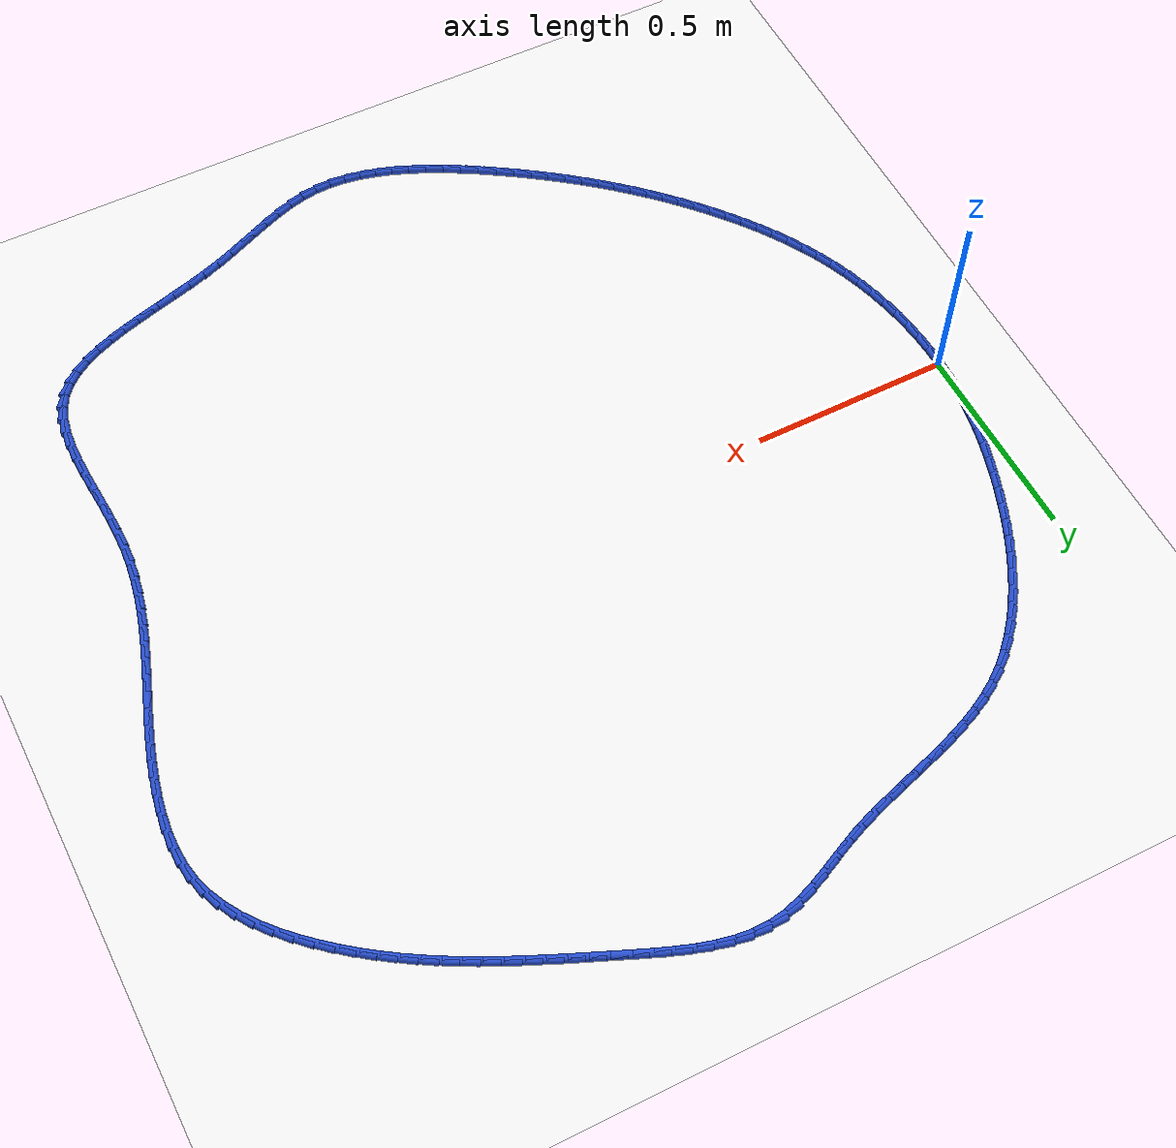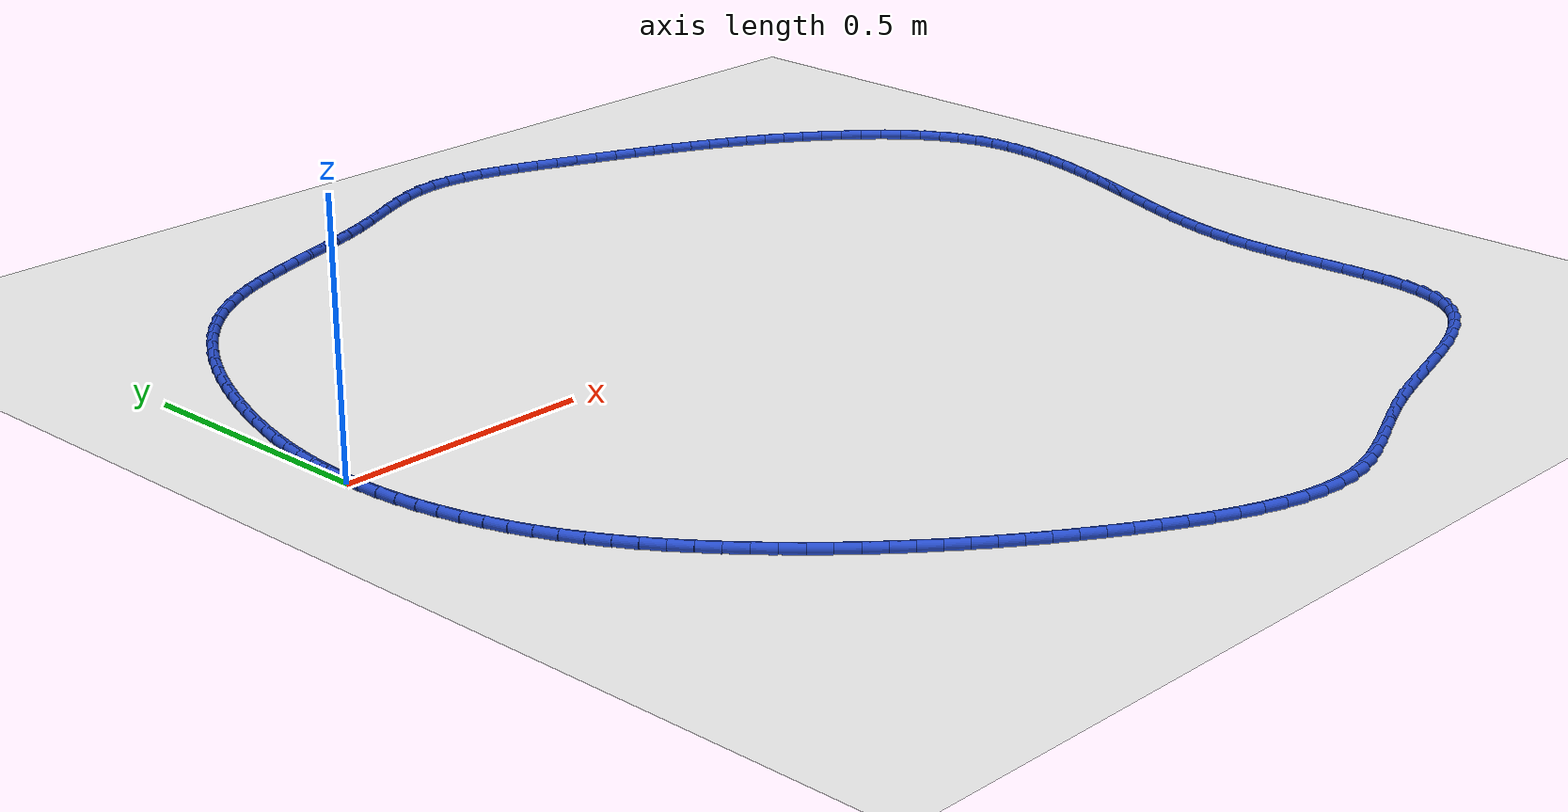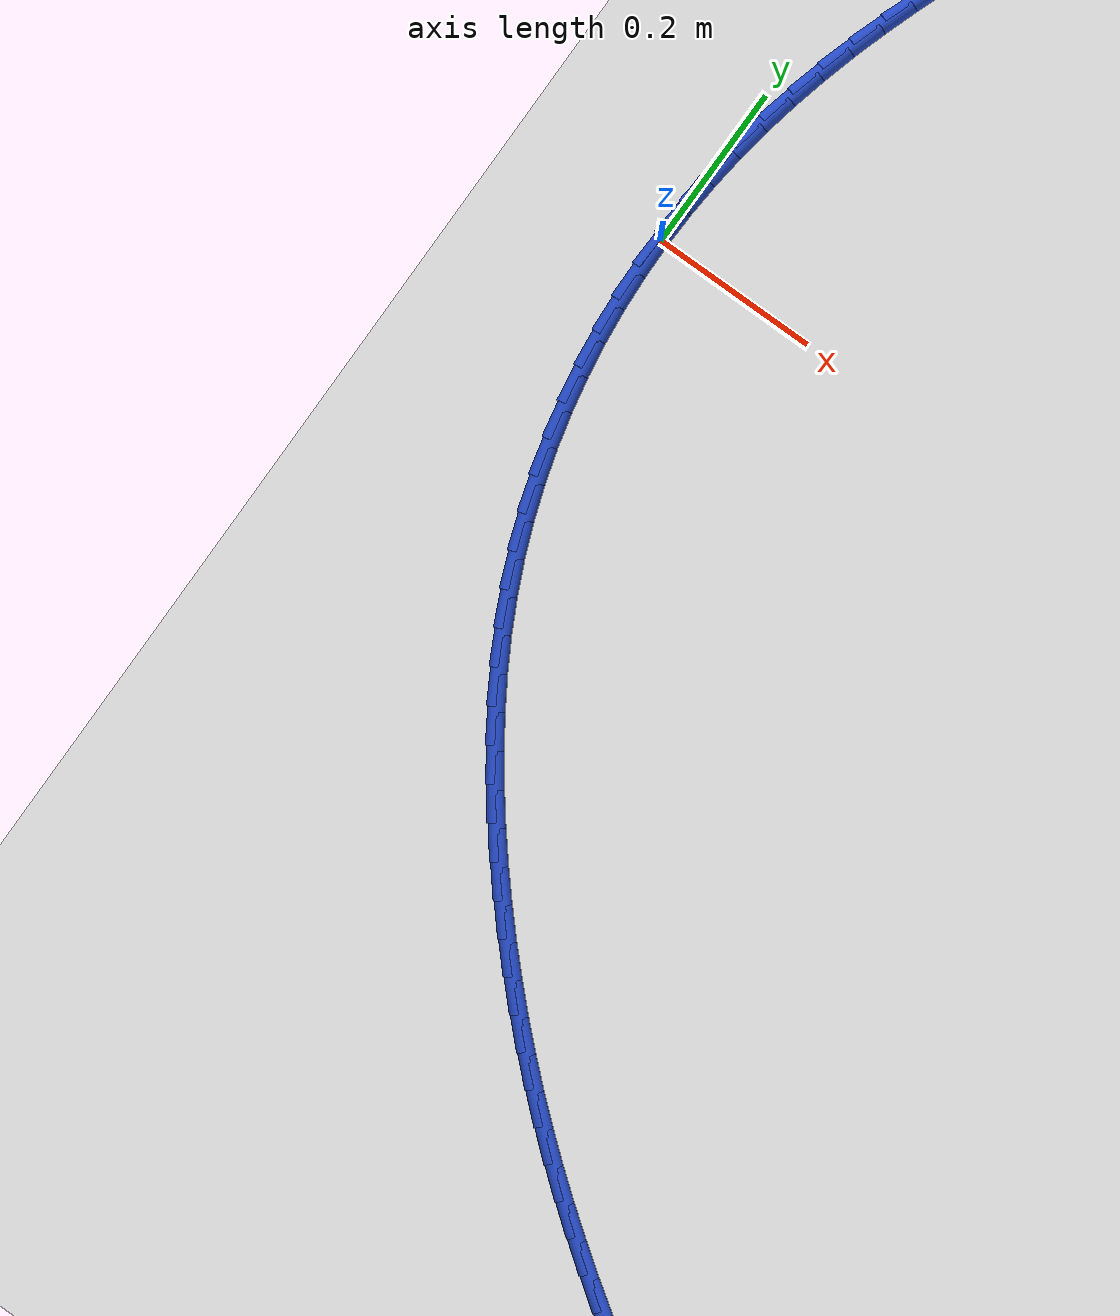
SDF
<sdf version="1.6">
 <world name="default">
  <light name="sun" type="directional">
   <pose>0 0 10 0 -0 0</pose>
   <diffuse>0.8 0.8 0.8 1</diffuse>
   <specular>0.2 0.2 0.2 1</specular>
   <attenuation>
    <range>1000</range>
    <constant>0.9</constant>
    <linear>0.01</linear>
    <quadratic>0.001</quadratic>
   </attenuation>
   <direction>-0.5 0.1 -0.9</direction>
  </light>
  <model name="ground_plane">
   <static>1</static>
   <link name="link">
    <collision name="collision">
     <geometry><plane><normal>0 0 1</normal><size>100 100</size></plane></geometry>
     <surface><friction><ode><mu>100</mu><mu2>50</mu2></ode></friction></surface>
    </collision>
    <visual name="visual">
     <cast_shadows>0</cast_shadows>
     <geometry><plane><normal>0 0 1</normal><size>100 100</size></plane></geometry>
     <material>
      <script><uri>file://media/materials/scripts/gazebo.material</uri><name>Gazebo/WhiteGlow</name></script>
     </material>
    </visual>
   </link>
  </model>
  <gravity>0 0 -9.8</gravity>
  <magnetic_field>6e-06 2.3e-05 -4.2e-05</magnetic_field>
  <atmosphere type="adiabatic"/>
  <physics name="default_physics" default="0" type="ode">
   <max_step_size>0.001</max_step_size>
   <real_time_factor>1</real_time_factor>
   <real_time_update_rate>1000</real_time_update_rate>
  </physics>
  <scene><ambient>0.4 0.4 0.4 1</ambient><background>0.7 0.7 0.7 1</background><shadows>1</shadows></scene>
  <spherical_coordinates>
   <surface_model>EARTH_WGS84</surface_model>
   <latitude_deg>0</latitude_deg>
   <longitude_deg>0</longitude_deg>
   <elevation>0</elevation>
   <heading_deg>0</heading_deg>
  </spherical_coordinates>
  <model name="line">
   <link name="link_0">
    <pose>8.673617379884035e-18 1.3877787807814457e-17 0.01 0 1.57 1.537599450367711</pose>
    <collision name="collision">
     <geometry><cylinder><radius>0.01</radius><length>0.08</length></cylinder></geometry>
    </collision>
    <visual name="visual">
     <material>
      <script><name>Gazebo/Blue</name><uri>file://media/materials/scripts/gazebo.material</uri></script>
     </material>
     <geometry><cylinder><radius>0.01</radius><length>0.08</length></cylinder></geometry>
    </visual>
   </link>
   <link name="link_1">
    <pose>0.0014228718258987249 0.04284587156562112 0.01 0 1.57 1.4931271198834803</pose>
    <collision name="collision">
     <geometry><cylinder><radius>0.01</radius><length>0.08</length></cylinder></geometry>
    </collision>
    <visual name="visual">
     <material>
      <script><name>Gazebo/Blue</name><uri>file://media/materials/scripts/gazebo.material</uri></script>
     </material>
     <geometry><cylinder><radius>0.01</radius><length>0.08</length></cylinder></geometry>
    </visual>
   </link>
   <link name="link_2">
    <pose>0.004742405994035064 0.08549928052376658 0.01 0 1.57 1.4502465807518221</pose>
    <collision name="collision">
     <geometry><cylinder><radius>0.01</radius><length>0.08</length></cylinder></geometry>
    </collision>
    <visual name="visual">
     <material>
      <script><name>Gazebo/Blue</name><uri>file://media/materials/scripts/gazebo.material</uri></script>
     </material>
     <geometry><cylinder><radius>0.01</radius><length>0.08</length></cylinder></geometry>
    </visual>
   </link>
   <link name="link_3">
    <pose>0.009887973836087992 0.12797650079125714 0.01 0 1.57 1.4091424649536322</pose>
    <collision name="collision">
     <geometry><cylinder><radius>0.01</radius><length>0.08</length></cylinder></geometry>
    </collision>
    <visual name="visual">
     <material>
      <script><name>Gazebo/Blue</name><uri>file://media/materials/scripts/gazebo.material</uri></script>
     </material>
     <geometry><cylinder><radius>0.01</radius><length>0.08</length></cylinder></geometry>
    </visual>
   </link>
   <link name="link_4">
    <pose>0.01678894668373644 0.17029380628491342 0.01 0 1.57 1.3699600547260784</pose>
    <collision name="collision">
     <geometry><cylinder><radius>0.01</radius><length>0.08</length></cylinder></geometry>
    </collision>
    <visual name="visual">
     <material>
      <script><name>Gazebo/Blue</name><uri>file://media/materials/scripts/gazebo.material</uri></script>
     </material>
     <geometry><cylinder><radius>0.01</radius><length>0.08</length></cylinder></geometry>
    </visual>
   </link>
   <link name="link_5">
    <pose>0.025374695868659362 0.2124674709215563 0.01 0 1.57 1.3328064204066152</pose>
    <collision name="collision">
     <geometry><cylinder><radius>0.01</radius><length>0.08</length></cylinder></geometry>
    </collision>
    <visual name="visual">
     <material>
      <script><name>Gazebo/Blue</name><uri>file://media/materials/scripts/gazebo.material</uri></script>
     </material>
     <geometry><cylinder><radius>0.01</radius><length>0.08</length></cylinder></geometry>
    </visual>
   </link>
   <link name="link_6">
    <pose>0.03557459272253571 0.2545137686180063 0.01 0 1.57 1.2977531604129349</pose>
    <collision name="collision">
     <geometry><cylinder><radius>0.01</radius><length>0.08</length></cylinder></geometry>
    </collision>
    <visual name="visual">
     <material>
      <script><name>Gazebo/Blue</name><uri>file://media/materials/scripts/gazebo.material</uri></script>
     </material>
     <geometry><cylinder><radius>0.01</radius><length>0.08</length></cylinder></geometry>
    </visual>
   </link>
   <link name="link_7">
    <pose>0.04731800857704441 0.2964489732910842 0.01 0 1.57 1.264840242945637</pose>
    <collision name="collision">
     <geometry><cylinder><radius>0.01</radius><length>0.08</length></cylinder></geometry>
    </collision>
    <visual name="visual">
     <material>
      <script><name>Gazebo/Blue</name><uri>file://media/materials/scripts/gazebo.material</uri></script>
     </material>
     <geometry><cylinder><radius>0.01</radius><length>0.08</length></cylinder></geometry>
    </visual>
   </link>
   <link name="link_8">
    <pose>0.06053431476386442 0.3382893588576108 0.01 0 1.57 1.234080470994198</pose>
    <collision name="collision">
     <geometry><cylinder><radius>0.01</radius><length>0.08</length></cylinder></geometry>
    </collision>
    <visual name="visual">
     <material>
      <script><name>Gazebo/Blue</name><uri>file://media/materials/scripts/gazebo.material</uri></script>
     </material>
     <geometry><cylinder><radius>0.01</radius><length>0.08</length></cylinder></geometry>
    </visual>
   </link>
   <link name="link_9">
    <pose>0.0751528826146747 0.3800511992344068 0.01 0 1.57 1.204846771785379</pose>
    <collision name="collision">
     <geometry><cylinder><radius>0.01</radius><length>0.08</length></cylinder></geometry>
    </collision>
    <visual name="visual">
     <material>
      <script><name>Gazebo/Blue</name><uri>file://media/materials/scripts/gazebo.material</uri></script>
     </material>
     <geometry><cylinder><radius>0.01</radius><length>0.08</length></cylinder></geometry>
    </visual>
   </link>
   <link name="link_10">
    <pose>0.09111874508139664 0.4217146082256782 0.01 0 1.57 1.1740229874519834</pose>
    <collision name="collision">
     <geometry><cylinder><radius>0.01</radius><length>0.08</length></cylinder></geometry>
    </collision>
    <visual name="visual">
     <material>
      <script><name>Gazebo/Blue</name><uri>file://media/materials/scripts/gazebo.material</uri></script>
     </material>
     <geometry><cylinder><radius>0.01</radius><length>0.08</length></cylinder></geometry>
    </visual>
   </link>
   <link name="link_11">
    <pose>0.10845266657797514 0.46308484810987344 0.01 0 1.57 1.1403853496866554</pose>
    <collision name="collision">
     <geometry><cylinder><radius>0.01</radius><length>0.08</length></cylinder></geometry>
    </collision>
    <visual name="visual">
     <material>
      <script><name>Gazebo/Blue</name><uri>file://media/materials/scripts/gazebo.material</uri></script>
     </material>
     <geometry><cylinder><radius>0.01</radius><length>0.08</length></cylinder></geometry>
    </visual>
   </link>
   <link name="link_12">
    <pose>0.12719827137774514 0.5039144014991548 0.01 0 1.57 1.1035539693658794</pose>
    <collision name="collision">
     <geometry><cylinder><radius>0.01</radius><length>0.08</length></cylinder></geometry>
    </collision>
    <visual name="visual">
     <material>
      <script><name>Gazebo/Blue</name><uri>file://media/materials/scripts/gazebo.material</uri></script>
     </material>
     <geometry><cylinder><radius>0.01</radius><length>0.08</length></cylinder></geometry>
    </visual>
   </link>
   <link name="link_13">
    <pose>0.14739918853467981 0.5439557399679742 0.01 0 1.57 1.0631086554477034</pose>
    <collision name="collision">
     <geometry><cylinder><radius>0.01</radius><length>0.08</length></cylinder></geometry>
    </collision>
    <visual name="visual">
     <material>
      <script><name>Gazebo/Blue</name><uri>file://media/materials/scripts/gazebo.material</uri></script>
     </material>
     <geometry><cylinder><radius>0.01</radius><length>0.08</length></cylinder></geometry>
    </visual>
   </link>
   <link name="link_14">
    <pose>0.16909904710275245 0.5829613350907845 0.01 0 1.57 1.018589851970601</pose>
    <collision name="collision">
     <geometry><cylinder><radius>0.01</radius><length>0.08</length></cylinder></geometry>
    </collision>
    <visual name="visual">
     <material>
      <script><name>Gazebo/Blue</name><uri>file://media/materials/scripts/gazebo.material</uri></script>
     </material>
     <geometry><cylinder><radius>0.01</radius><length>0.08</length></cylinder></geometry>
    </visual>
   </link>
   <link name="link_15">
    <pose>0.19234147613593622 0.6206836584420379 0.01 0 1.57 0.9695048950105307</pose>
    <collision name="collision">
     <geometry><cylinder><radius>0.01</radius><length>0.08</length></cylinder></geometry>
    </collision>
    <visual name="visual">
     <material>
      <script><name>Gazebo/Blue</name><uri>file://media/materials/scripts/gazebo.material</uri></script>
     </material>
     <geometry><cylinder><radius>0.01</radius><length>0.08</length></cylinder></geometry>
    </visual>
   </link>
   <link name="link_16">
    <pose>0.21717010468820444 0.6568751815961871 0.01 0 1.57 0.9153422922503045</pose>
    <collision name="collision">
     <geometry><cylinder><radius>0.01</radius><length>0.08</length></cylinder></geometry>
    </collision>
    <visual name="visual">
     <material>
      <script><name>Gazebo/Blue</name><uri>file://media/materials/scripts/gazebo.material</uri></script>
     </material>
     <geometry><cylinder><radius>0.01</radius><length>0.08</length></cylinder></geometry>
    </visual>
   </link>
   <link name="link_17">
    <pose>0.2436285618135302 0.691288376127684 0.01 0 1.57 0.8555978114216262</pose>
    <collision name="collision">
     <geometry><cylinder><radius>0.01</radius><length>0.08</length></cylinder></geometry>
    </collision>
    <visual name="visual">
     <material>
      <script><name>Gazebo/Blue</name><uri>file://media/materials/scripts/gazebo.material</uri></script>
     </material>
     <geometry><cylinder><radius>0.01</radius><length>0.08</length></cylinder></geometry>
    </visual>
   </link>
   <link name="link_18">
    <pose>0.2717604765658868 0.7236757136109813 0.01 0 1.57 0.7898167057926905</pose>
    <collision name="collision">
     <geometry><cylinder><radius>0.01</radius><length>0.08</length></cylinder></geometry>
    </collision>
    <visual name="visual">
     <material>
      <script><name>Gazebo/Blue</name><uri>file://media/materials/scripts/gazebo.material</uri></script>
     </material>
     <geometry><cylinder><radius>0.01</radius><length>0.08</length></cylinder></geometry>
    </visual>
   </link>
   <link name="link_19">
    <pose>0.3016094779992475 0.7537896656205313 0.01 0 1.57 0.7176558269763292</pose>
    <collision name="collision">
     <geometry><cylinder><radius>0.01</radius><length>0.08</length></cylinder></geometry>
    </collision>
    <visual name="visual">
     <material>
      <script><name>Gazebo/Blue</name><uri>file://media/materials/scripts/gazebo.material</uri></script>
     </material>
     <geometry><cylinder><radius>0.01</radius><length>0.08</length></cylinder></geometry>
    </visual>
   </link>
   <link name="link_20">
    <pose>0.33321919516758536 0.7813827037307866 0.01 0 1.57 0.6389675547448508</pose>
    <collision name="collision">
     <geometry><cylinder><radius>0.01</radius><length>0.08</length></cylinder></geometry>
    </collision>
    <visual name="visual">
     <material>
      <script><name>Gazebo/Blue</name><uri>file://media/materials/scripts/gazebo.material</uri></script>
     </material>
     <geometry><cylinder><radius>0.01</radius><length>0.08</length></cylinder></geometry>
    </visual>
   </link>
   <link name="link_21">
    <pose>0.3666332401087448 0.8062073435570297 0.01 0 1.57 0.5573835775006121</pose>
    <collision name="collision">
     <geometry><cylinder><radius>0.01</radius><length>0.08</length></cylinder></geometry>
    </collision>
    <visual name="visual">
     <material>
      <script><name>Gazebo/Blue</name><uri>file://media/materials/scripts/gazebo.material</uri></script>
     </material>
     <geometry><cylinder><radius>0.01</radius><length>0.08</length></cylinder></geometry>
    </visual>
   </link>
   <link name="link_22">
    <pose>0.4018421612449245 0.8281534389833063 0.01 0 1.57 0.48485346961716697</pose>
    <collision name="collision">
     <geometry><cylinder><radius>0.01</radius><length>0.08</length></cylinder></geometry>
    </collision>
    <visual name="visual">
     <material>
      <script><name>Gazebo/Blue</name><uri>file://media/materials/scripts/gazebo.material</uri></script>
     </material>
     <geometry><cylinder><radius>0.01</radius><length>0.08</length></cylinder></geometry>
    </visual>
   </link>
   <link name="link_23">
    <pose>0.43866602477117095 0.8475520828414268 0.01 0 1.57 0.4243671857226578</pose>
    <collision name="collision">
     <geometry><cylinder><radius>0.01</radius><length>0.08</length></cylinder></geometry>
    </collision>
    <visual name="visual">
     <material>
      <script><name>Gazebo/Blue</name><uri>file://media/materials/scripts/gazebo.material</uri></script>
     </material>
     <geometry><cylinder><radius>0.01</radius><length>0.08</length></cylinder></geometry>
    </visual>
   </link>
   <link name="link_24">
    <pose>0.47689072773646457 0.8648228039151946 0.01 0 1.57 0.3760746621710777</pose>
    <collision name="collision">
     <geometry><cylinder><radius>0.01</radius><length>0.08</length></cylinder></geometry>
    </collision>
    <visual name="visual">
     <material>
      <script><name>Gazebo/Blue</name><uri>file://media/materials/scripts/gazebo.material</uri></script>
     </material>
     <geometry><cylinder><radius>0.01</radius><length>0.08</length></cylinder></geometry>
    </visual>
   </link>
   <link name="link_25">
    <pose>0.5163021671897856 0.8803851309884123 0.01 0 1.57 0.33973864782732827</pose>
    <collision name="collision">
     <geometry><cylinder><radius>0.01</radius><length>0.08</length></cylinder></geometry>
    </collision>
    <visual name="visual">
     <material>
      <script><name>Gazebo/Blue</name><uri>file://media/materials/scripts/gazebo.material</uri></script>
     </material>
     <geometry><cylinder><radius>0.01</radius><length>0.08</length></cylinder></geometry>
    </visual>
   </link>
   <link name="link_26">
    <pose>0.5566862401801154 0.8946585928448834 0.01 0 1.57 0.31495233899846786</pose>
    <collision name="collision">
     <geometry><cylinder><radius>0.01</radius><length>0.08</length></cylinder></geometry>
    </collision>
    <visual name="visual">
     <material>
      <script><name>Gazebo/Blue</name><uri>file://media/materials/scripts/gazebo.material</uri></script>
     </material>
     <geometry><cylinder><radius>0.01</radius><length>0.08</length></cylinder></geometry>
    </visual>
   </link>
   <link name="link_27">
    <pose>0.5978288437564337 0.9080627182684106 0.01 0 1.57 0.3012913620824555</pose>
    <collision name="collision">
     <geometry><cylinder><radius>0.01</radius><length>0.08</length></cylinder></geometry>
    </collision>
    <visual name="visual">
     <material>
      <script><name>Gazebo/Blue</name><uri>file://media/materials/scripts/gazebo.material</uri></script>
     </material>
     <geometry><cylinder><radius>0.01</radius><length>0.08</length></cylinder></geometry>
    </visual>
   </link>
   <link name="link_28">
    <pose>0.6395158749677219 0.9210170360427972 0.01 0 1.57 0.29840373892915856</pose>
    <collision name="collision">
     <geometry><cylinder><radius>0.01</radius><length>0.08</length></cylinder></geometry>
    </collision>
    <visual name="visual">
     <material>
      <script><name>Gazebo/Blue</name><uri>file://media/materials/scripts/gazebo.material</uri></script>
     </material>
     <geometry><cylinder><radius>0.01</radius><length>0.08</length></cylinder></geometry>
    </visual>
   </link>
   <link name="link_29">
    <pose>0.6815332308629598 0.933941074951846 0.01 0 1.57 0.3060504058377907</pose>
    <collision name="collision">
     <geometry><cylinder><radius>0.01</radius><length>0.08</length></cylinder></geometry>
    </collision>
    <visual name="visual">
     <material>
      <script><name>Gazebo/Blue</name><uri>file://media/materials/scripts/gazebo.material</uri></script>
     </material>
     <geometry><cylinder><radius>0.01</radius><length>0.08</length></cylinder></geometry>
    </visual>
   </link>
   <link name="link_30">
    <pose>0.7236668084911281 0.9472543637793599 0.01 0 1.57 0.3241074506008348</pose>
    <collision name="collision">
     <geometry><cylinder><radius>0.01</radius><length>0.08</length></cylinder></geometry>
    </collision>
    <visual name="visual">
     <material>
      <script><name>Gazebo/Blue</name><uri>file://media/materials/scripts/gazebo.material</uri></script>
     </material>
     <geometry><cylinder><radius>0.01</radius><length>0.08</length></cylinder></geometry>
    </visual>
   </link>
   <link name="link_31">
    <pose>0.7657025049012077 0.9613764313091424 0.01 0 1.57 0.35253620106476874</pose>
    <collision name="collision">
     <geometry><cylinder><radius>0.01</radius><length>0.08</length></cylinder></geometry>
    </collision>
    <visual name="visual">
     <material>
      <script><name>Gazebo/Blue</name><uri>file://media/materials/scripts/gazebo.material</uri></script>
     </material>
     <geometry><cylinder><radius>0.01</radius><length>0.08</length></cylinder></geometry>
    </visual>
   </link>
   <link name="link_32">
    <pose>0.807426217142179 0.9767268063249963 0.01 0 1.57 0.3912274073067997</pose>
    <collision name="collision">
     <geometry><cylinder><radius>0.01</radius><length>0.08</length></cylinder></geometry>
    </collision>
    <visual name="visual">
     <material>
      <script><name>Gazebo/Blue</name><uri>file://media/materials/scripts/gazebo.material</uri></script>
     </material>
     <geometry><cylinder><radius>0.01</radius><length>0.08</length></cylinder></geometry>
    </visual>
   </link>
   <link name="link_33">
    <pose>0.84862485487194 0.9937208504358417 0.01 0 1.57 0.42770603930208484</pose>
    <collision name="collision">
     <geometry><cylinder><radius>0.01</radius><length>0.08</length></cylinder></geometry>
    </collision>
    <visual name="visual">
     <material>
      <script><name>Gazebo/Blue</name><uri>file://media/materials/scripts/gazebo.material</uri></script>
     </material>
     <geometry><cylinder><radius>0.01</radius><length>0.08</length></cylinder></geometry>
    </visual>
   </link>
   <link name="link_34">
    <pose>0.8892186142266436 1.0122254133276047 0.01 0 1.57 0.43752843359220994</pose>
    <collision name="collision">
     <geometry><cylinder><radius>0.01</radius><length>0.08</length></cylinder></geometry>
    </collision>
    <visual name="visual">
     <material>
      <script><name>Gazebo/Blue</name><uri>file://media/materials/scripts/gazebo.material</uri></script>
     </material>
     <geometry><cylinder><radius>0.01</radius><length>0.08</length></cylinder></geometry>
    </visual>
   </link>
   <link name="link_35">
    <pose>0.9293925530836605 1.0310173629798542 0.01 0 1.57 0.41744703278493184</pose>
    <collision name="collision">
     <geometry><cylinder><radius>0.01</radius><length>0.08</length></cylinder></geometry>
    </collision>
    <visual name="visual">
     <material>
      <script><name>Gazebo/Blue</name><uri>file://media/materials/scripts/gazebo.material</uri></script>
     </material>
     <geometry><cylinder><radius>0.01</radius><length>0.08</length></cylinder></geometry>
    </visual>
   </link>
   <link name="link_36">
    <pose>0.9693630146237355 1.0487448194140832 0.01 0 1.57 0.36571064796944036</pose>
    <collision name="collision">
     <geometry><cylinder><radius>0.01</radius><length>0.08</length></cylinder></geometry>
    </collision>
    <visual name="visual">
     <material>
      <script><name>Gazebo/Blue</name><uri>file://media/materials/scripts/gazebo.material</uri></script>
     </material>
     <geometry><cylinder><radius>0.01</radius><length>0.08</length></cylinder></geometry>
    </visual>
   </link>
   <link name="link_37">
    <pose>1.0093463420276125 1.0640559026517835 0.01 0 1.57 0.2795300269030682</pose>
    <collision name="collision">
     <geometry><cylinder><radius>0.01</radius><length>0.08</length></cylinder></geometry>
    </collision>
    <visual name="visual">
     <material>
      <script><name>Gazebo/Blue</name><uri>file://media/materials/scripts/gazebo.material</uri></script>
     </material>
     <geometry><cylinder><radius>0.01</radius><length>0.08</length></cylinder></geometry>
    </visual>
   </link>
   <link name="link_38">
    <pose>1.0495588784760357 1.075598732714448 0.01 0 1.57 0.1567691778716241</pose>
    <collision name="collision">
     <geometry><cylinder><radius>0.01</radius><length>0.08</length></cylinder></geometry>
    </collision>
    <visual name="visual">
     <material>
      <script><name>Gazebo/Blue</name><uri>file://media/materials/scripts/gazebo.material</uri></script>
     </material>
     <geometry><cylinder><radius>0.01</radius><length>0.08</length></cylinder></geometry>
    </visual>
   </link>
   <link name="link_39">
    <pose>1.0902163374289144 1.0820253032894367 0.01 0 1.57 0.01487435224394456</pose>
    <collision name="collision">
     <geometry><cylinder><radius>0.01</radius><length>0.08</length></cylinder></geometry>
    </collision>
    <visual name="visual">
     <material>
      <script><name>Gazebo/Blue</name><uri>file://media/materials/scripts/gazebo.material</uri></script>
     </material>
     <geometry><cylinder><radius>0.01</radius><length>0.08</length></cylinder></geometry>
    </visual>
   </link>
   <link name="link_40">
    <pose>1.1314286439705985 1.0826383548661989 0.01 0 1.57 -0.10813326937899687</pose>
    <collision name="collision">
     <geometry><cylinder><radius>0.01</radius><length>0.08</length></cylinder></geometry>
    </collision>
    <visual name="visual">
     <material>
      <script><name>Gazebo/Blue</name><uri>file://media/materials/scripts/gazebo.material</uri></script>
     </material>
     <geometry><cylinder><radius>0.01</radius><length>0.08</length></cylinder></geometry>
    </visual>
   </link>
   <link name="link_41">
    <pose>1.173082038984183 1.0781165993287316 0.01 0 1.57 -0.206830549898252</pose>
    <collision name="collision">
     <geometry><cylinder><radius>0.01</radius><length>0.08</length></cylinder></geometry>
    </collision>
    <visual name="visual">
     <material>
      <script><name>Gazebo/Blue</name><uri>file://media/materials/scripts/gazebo.material</uri></script>
     </material>
     <geometry><cylinder><radius>0.01</radius><length>0.08</length></cylinder></geometry>
    </visual>
   </link>
   <link name="link_42">
    <pose>1.2150343224524427 1.0693136999659842 0.01 0 1.57 -0.28266871808706434</pose>
    <collision name="collision">
     <geometry><cylinder><radius>0.01</radius><length>0.08</length></cylinder></geometry>
    </collision>
    <visual name="visual">
     <material>
      <script><name>Gazebo/Blue</name><uri>file://media/materials/scripts/gazebo.material</uri></script>
     </material>
     <geometry><cylinder><radius>0.01</radius><length>0.08</length></cylinder></geometry>
    </visual>
   </link>
   <link name="link_43">
    <pose>1.257143294358152 1.0570833200669048 0.01 0 1.57 -0.3379640296120597</pose>
    <collision name="collision">
     <geometry><cylinder><radius>0.01</radius><length>0.08</length></cylinder></geometry>
    </collision>
    <visual name="visual">
     <material>
      <script><name>Gazebo/Blue</name><uri>file://media/materials/scripts/gazebo.material</uri></script>
     </material>
     <geometry><cylinder><radius>0.01</radius><length>0.08</length></cylinder></geometry>
    </visual>
   </link>
   <link name="link_44">
    <pose>1.2992667546840877 1.0422791229204424 0.01 0 1.57 -0.37487027529283395</pose>
    <collision name="collision">
     <geometry><cylinder><radius>0.01</radius><length>0.08</length></cylinder></geometry>
    </collision>
    <visual name="visual">
     <material>
      <script><name>Gazebo/Blue</name><uri>file://media/materials/scripts/gazebo.material</uri></script>
     </material>
     <geometry><cylinder><radius>0.01</radius><length>0.08</length></cylinder></geometry>
    </visual>
   </link>
   <link name="link_45">
    <pose>1.3412625034130226 1.0257547718155455 0.01 0 1.57 -0.3948947770489714</pose>
    <collision name="collision">
     <geometry><cylinder><radius>0.01</radius><length>0.08</length></cylinder></geometry>
    </collision>
    <visual name="visual">
     <material>
      <script><name>Gazebo/Blue</name><uri>file://media/materials/scripts/gazebo.material</uri></script>
     </material>
     <geometry><cylinder><radius>0.01</radius><length>0.08</length></cylinder></geometry>
    </visual>
   </link>
   <link name="link_46">
    <pose>1.3829883405277337 1.0083639300411626 0.01 0 1.57 -0.3998123739078284</pose>
    <collision name="collision">
     <geometry><cylinder><radius>0.01</radius><length>0.08</length></cylinder></geometry>
    </collision>
    <visual name="visual">
     <material>
      <script><name>Gazebo/Blue</name><uri>file://media/materials/scripts/gazebo.material</uri></script>
     </material>
     <geometry><cylinder><radius>0.01</radius><length>0.08</length></cylinder></geometry>
    </visual>
   </link>
   <link name="link_47">
    <pose>1.424309677556677 0.9909026870659385 0.01 0 1.57 -0.40101207421590196</pose>
    <collision name="collision">
     <geometry><cylinder><radius>0.01</radius><length>0.08</length></cylinder></geometry>
    </collision>
    <visual name="visual">
     <material>
      <script><name>Gazebo/Blue</name><uri>file://media/materials/scripts/gazebo.material</uri></script>
     </material>
     <geometry><cylinder><radius>0.01</radius><length>0.08</length></cylinder></geometry>
    </visual>
   </link>
   <link name="link_48">
    <pose>1.4651697376489927 0.9735785643522845 0.01 0 1.57 -0.40520815230029555</pose>
    <collision name="collision">
     <geometry><cylinder><radius>0.01</radius><length>0.08</length></cylinder></geometry>
    </collision>
    <visual name="visual">
     <material>
      <script><name>Gazebo/Blue</name><uri>file://media/materials/scripts/gazebo.material</uri></script>
     </material>
     <geometry><cylinder><radius>0.01</radius><length>0.08</length></cylinder></geometry>
    </visual>
   </link>
   <link name="link_49">
    <pose>1.5055573019600175 0.9562544820724649 0.01 0 1.57 -0.41256374679476904</pose>
    <collision name="collision">
     <geometry><cylinder><radius>0.01</radius><length>0.08</length></cylinder></geometry>
    </collision>
    <visual name="visual">
     <material>
      <script><name>Gazebo/Blue</name><uri>file://media/materials/scripts/gazebo.material</uri></script>
     </material>
     <geometry><cylinder><radius>0.01</radius><length>0.08</length></cylinder></geometry>
    </visual>
   </link>
   <link name="link_50">
    <pose>1.545461727178648 0.938789007056181 0.01 0 1.57 -0.42313899793170695</pose>
    <collision name="collision">
     <geometry><cylinder><radius>0.01</radius><length>0.08</length></cylinder></geometry>
    </collision>
    <visual name="visual">
     <material>
      <script><name>Gazebo/Blue</name><uri>file://media/materials/scripts/gazebo.material</uri></script>
     </material>
     <geometry><cylinder><radius>0.01</radius><length>0.08</length></cylinder></geometry>
    </visual>
   </link>
   <link name="link_51">
    <pose>1.5848723699937823 0.9210407061331355 0.01 0 1.57 -0.4369716728732286</pose>
    <collision name="collision">
     <geometry><cylinder><radius>0.01</radius><length>0.08</length></cylinder></geometry>
    </collision>
    <visual name="visual">
     <material>
      <script><name>Gazebo/Blue</name><uri>file://media/materials/scripts/gazebo.material</uri></script>
     </material>
     <geometry><cylinder><radius>0.01</radius><length>0.08</length></cylinder></geometry>
    </visual>
   </link>
   <link name="link_52">
    <pose>1.623778587094316 0.9028681461330307 0.01 0 1.57 -0.45407254224297905</pose>
    <collision name="collision">
     <geometry><cylinder><radius>0.01</radius><length>0.08</length></cylinder></geometry>
    </collision>
    <visual name="visual">
     <material>
      <script><name>Gazebo/Blue</name><uri>file://media/materials/scripts/gazebo.material</uri></script>
     </material>
     <geometry><cylinder><radius>0.01</radius><length>0.08</length></cylinder></geometry>
    </visual>
   </link>
   <link name="link_53">
    <pose>1.6621697351691465 0.8841298938855683 0.01 0 1.57 -0.4744200437202296</pose>
    <collision name="collision">
     <geometry><cylinder><radius>0.01</radius><length>0.08</length></cylinder></geometry>
    </collision>
    <visual name="visual">
     <material>
      <script><name>Gazebo/Blue</name><uri>file://media/materials/scripts/gazebo.material</uri></script>
     </material>
     <geometry><cylinder><radius>0.01</radius><length>0.08</length></cylinder></geometry>
    </visual>
   </link>
   <link name="link_54">
    <pose>1.7000351709071706 0.8646845162204513 0.01 0 1.57 -0.49795452736878637</pose>
    <collision name="collision">
     <geometry><cylinder><radius>0.01</radius><length>0.08</length></cylinder></geometry>
    </collision>
    <visual name="visual">
     <material>
      <script><name>Gazebo/Blue</name><uri>file://media/materials/scripts/gazebo.material</uri></script>
     </material>
     <geometry><cylinder><radius>0.01</radius><length>0.08</length></cylinder></geometry>
    </visual>
   </link>
   <link name="link_55">
    <pose>1.7373642509972864 0.844390579967382 0.01 0 1.57 -0.5245725518492229</pose>
    <collision name="collision">
     <geometry><cylinder><radius>0.01</radius><length>0.08</length></cylinder></geometry>
    </collision>
    <visual name="visual">
     <material>
      <script><name>Gazebo/Blue</name><uri>file://media/materials/scripts/gazebo.material</uri></script>
     </material>
     <geometry><cylinder><radius>0.01</radius><length>0.08</length></cylinder></geometry>
    </visual>
   </link>
   <link name="link_56">
    <pose>1.7741463321283897 0.823106651956062 0.01 0 1.57 -0.5541218759405149</pose>
    <collision name="collision">
     <geometry><cylinder><radius>0.01</radius><length>0.08</length></cylinder></geometry>
    </collision>
    <visual name="visual">
     <material>
      <script><name>Gazebo/Blue</name><uri>file://media/materials/scripts/gazebo.material</uri></script>
     </material>
     <geometry><cylinder><radius>0.01</radius><length>0.08</length></cylinder></geometry>
    </visual>
   </link>
   <link name="link_57">
    <pose>1.8103707709893775 0.8006912990161942 0.01 0 1.57 -0.5863979294713135</pose>
    <collision name="collision">
     <geometry><cylinder><radius>0.01</radius><length>0.08</length></cylinder></geometry>
    </collision>
    <visual name="visual">
     <material>
      <script><name>Gazebo/Blue</name><uri>file://media/materials/scripts/gazebo.material</uri></script>
     </material>
     <geometry><cylinder><radius>0.01</radius><length>0.08</length></cylinder></geometry>
    </visual>
   </link>
   <link name="link_58">
    <pose>1.8460269242691476 0.7770030879774804 0.01 0 1.57 -0.621142603829005</pose>
    <collision name="collision">
     <geometry><cylinder><radius>0.01</radius><length>0.08</length></cylinder></geometry>
    </collision>
    <visual name="visual">
     <material>
      <script><name>Gazebo/Blue</name><uri>file://media/materials/scripts/gazebo.material</uri></script>
     </material>
     <geometry><cylinder><radius>0.01</radius><length>0.08</length></cylinder></geometry>
    </visual>
   </link>
   <link name="link_59">
    <pose>1.8811041486565965 0.7519005856696236 0.01 0 1.57 -0.6580461251453021</pose>
    <collision name="collision">
     <geometry><cylinder><radius>0.01</radius><length>0.08</length></cylinder></geometry>
    </collision>
    <visual name="visual">
     <material>
      <script><name>Gazebo/Blue</name><uri>file://media/materials/scripts/gazebo.material</uri></script>
     </material>
     <geometry><cylinder><radius>0.01</radius><length>0.08</length></cylinder></geometry>
    </visual>
   </link>
   <link name="link_60">
    <pose>1.915591800840621 0.7252423589223252 0.01 0 1.57 -0.6968840890273211</pose>
    <collision name="collision">
     <geometry><cylinder><radius>0.01</radius><length>0.08</length></cylinder></geometry>
    </collision>
    <visual name="visual">
     <material>
      <script><name>Gazebo/Blue</name><uri>file://media/materials/scripts/gazebo.material</uri></script>
     </material>
     <geometry><cylinder><radius>0.01</radius><length>0.08</length></cylinder></geometry>
    </visual>
   </link>
   <link name="link_61">
    <pose>1.9494662979429587 0.6968902241717155 0.01 0 1.57 -0.7406611730187971</pose>
    <collision name="collision">
     <geometry><cylinder><radius>0.01</radius><length>0.08</length></cylinder></geometry>
    </collision>
    <visual name="visual">
     <material>
      <script><name>Gazebo/Blue</name><uri>file://media/materials/scripts/gazebo.material</uri></script>
     </material>
     <geometry><cylinder><radius>0.01</radius><length>0.08</length></cylinder></geometry>
    </visual>
   </link>
   <link name="link_62">
    <pose>1.9823947135604896 0.6667836855148987 0.01 0 1.57 -0.7934497828985574</pose>
    <collision name="collision">
     <geometry><cylinder><radius>0.01</radius><length>0.08</length></cylinder></geometry>
    </collision>
    <visual name="visual">
     <material>
      <script><name>Gazebo/Blue</name><uri>file://media/materials/scripts/gazebo.material</uri></script>
     </material>
     <geometry><cylinder><radius>0.01</radius><length>0.08</length></cylinder></geometry>
    </visual>
   </link>
   <link name="link_63">
    <pose>2.013728115245792 0.6349416079163096 0.01 0 1.57 -0.856807101548687</pose>
    <collision name="collision">
     <geometry><cylinder><radius>0.01</radius><length>0.08</length></cylinder></geometry>
    </collision>
    <visual name="visual">
     <material>
      <script><name>Gazebo/Blue</name><uri>file://media/materials/scripts/gazebo.material</uri></script>
     </material>
     <geometry><cylinder><radius>0.01</radius><length>0.08</length></cylinder></geometry>
    </visual>
   </link>
   <link name="link_64">
    <pose>2.042803298290719 0.601386440635717 0.01 0 1.57 -0.9324098346143711</pose>
    <collision name="collision">
     <geometry><cylinder><radius>0.01</radius><length>0.08</length></cylinder></geometry>
    </collision>
    <visual name="visual">
     <material>
      <script><name>Gazebo/Blue</name><uri>file://media/materials/scripts/gazebo.material</uri></script>
     </material>
     <geometry><cylinder><radius>0.01</radius><length>0.08</length></cylinder></geometry>
    </visual>
   </link>
   <link name="link_65">
    <pose>2.068957057987124 0.5661406329328889 0.01 0 1.57 -1.0220383351015123</pose>
    <collision name="collision">
     <geometry><cylinder><radius>0.01</radius><length>0.08</length></cylinder></geometry>
    </collision>
    <visual name="visual">
     <material>
      <script><name>Gazebo/Blue</name><uri>file://media/materials/scripts/gazebo.material</uri></script>
     </material>
     <geometry><cylinder><radius>0.01</radius><length>0.08</length></cylinder></geometry>
    </visual>
   </link>
   <link name="link_66">
    <pose>2.0915261896268595 0.529226634067593 0.01 0 1.57 -1.1272332688428837</pose>
    <collision name="collision">
     <geometry><cylinder><radius>0.01</radius><length>0.08</length></cylinder></geometry>
    </collision>
    <visual name="visual">
     <material>
      <script><name>Gazebo/Blue</name><uri>file://media/materials/scripts/gazebo.material</uri></script>
     </material>
     <geometry><cylinder><radius>0.01</radius><length>0.08</length></cylinder></geometry>
    </visual>
   </link>
   <link name="link_67">
    <pose>2.109847488501779 0.49066689329959845 0.01 0 1.57 -1.2486893150940497</pose>
    <collision name="collision">
     <geometry><cylinder><radius>0.01</radius><length>0.08</length></cylinder></geometry>
    </collision>
    <visual name="visual">
     <material>
      <script><name>Gazebo/Blue</name><uri>file://media/materials/scripts/gazebo.material</uri></script>
     </material>
     <geometry><cylinder><radius>0.01</radius><length>0.08</length></cylinder></geometry>
    </visual>
   </link>
   <link name="link_68">
    <pose>2.1232577499037353 0.45048385988867284 0.01 0 1.57 -1.3804274237488203</pose>
    <collision name="collision">
     <geometry><cylinder><radius>0.01</radius><length>0.08</length></cylinder></geometry>
    </collision>
    <visual name="visual">
     <material>
      <script><name>Gazebo/Blue</name><uri>file://media/materials/scripts/gazebo.material</uri></script>
     </material>
     <geometry><cylinder><radius>0.01</radius><length>0.08</length></cylinder></geometry>
    </visual>
   </link>
   <link name="link_69">
    <pose>2.131296763287441 0.40876661677939596 0.01 0 1.57 -1.497668811316208</pose>
    <collision name="collision">
     <geometry><cylinder><radius>0.01</radius><length>0.08</length></cylinder></geometry>
    </collision>
    <visual name="visual">
     <material>
      <script><name>Gazebo/Blue</name><uri>file://media/materials/scripts/gazebo.material</uri></script>
     </material>
     <geometry><cylinder><radius>0.01</radius><length>0.08</length></cylinder></geometry>
    </visual>
   </link>
   <link name="link_70">
    <pose>2.1344363458209 0.3659101889198381 0.01 0 1.57 1.547343123283973</pose>
    <collision name="collision">
     <geometry><cylinder><radius>0.01</radius><length>0.08</length></cylinder></geometry>
    </collision>
    <visual name="visual">
     <material>
      <script><name>Gazebo/Blue</name><uri>file://media/materials/scripts/gazebo.material</uri></script>
     </material>
     <geometry><cylinder><radius>0.01</radius><length>0.08</length></cylinder></geometry>
    </visual>
   </link>
   <link name="link_71">
    <pose>2.1334156432709137 0.32239735299113603 0.01 0 1.57 1.4694695702363008</pose>
    <collision name="collision">
     <geometry><cylinder><radius>0.01</radius><length>0.08</length></cylinder></geometry>
    </collision>
    <visual name="visual">
     <material>
      <script><name>Gazebo/Blue</name><uri>file://media/materials/scripts/gazebo.material</uri></script>
     </material>
     <geometry><cylinder><radius>0.01</radius><length>0.08</length></cylinder></geometry>
    </visual>
   </link>
   <link name="link_72">
    <pose>2.128973824017783 0.278710893097403 0.01 0 1.57 1.4080213315824655</pose>
    <collision name="collision">
     <geometry><cylinder><radius>0.01</radius><length>0.08</length></cylinder></geometry>
    </collision>
    <visual name="visual">
     <material>
      <script><name>Gazebo/Blue</name><uri>file://media/materials/scripts/gazebo.material</uri></script>
     </material>
     <geometry><cylinder><radius>0.01</radius><length>0.08</length></cylinder></geometry>
    </visual>
   </link>
   <link name="link_73">
    <pose>2.121850056441805 0.2353335933427498 0.01 0 1.57 1.360372979010108</pose>
    <collision name="collision">
     <geometry><cylinder><radius>0.01</radius><length>0.08</length></cylinder></geometry>
    </collision>
    <visual name="visual">
     <material>
      <script><name>Gazebo/Blue</name><uri>file://media/materials/scripts/gazebo.material</uri></script>
     </material>
     <geometry><cylinder><radius>0.01</radius><length>0.08</length></cylinder></geometry>
    </visual>
   </link>
   <link name="link_74">
    <pose>2.11274174879832 0.1926887218184892 0.01 0 1.57 1.3212506566330535</pose>
    <collision name="collision">
     <geometry><cylinder><radius>0.01</radius><length>0.08</length></cylinder></geometry>
    </collision>
    <visual name="visual">
     <material>
      <script><name>Gazebo/Blue</name><uri>file://media/materials/scripts/gazebo.material</uri></script>
     </material>
     <geometry><cylinder><radius>0.01</radius><length>0.08</length></cylinder></geometry>
    </visual>
   </link>
   <link name="link_75">
    <pose>2.102066134160256 0.15080024441653148 0.01 0 1.57 1.2891659754196472</pose>
    <collision name="collision">
     <geometry><cylinder><radius>0.01</radius><length>0.08</length></cylinder></geometry>
    </collision>
    <visual name="visual">
     <material>
      <script><name>Gazebo/Blue</name><uri>file://media/materials/scripts/gazebo.material</uri></script>
     </material>
     <geometry><cylinder><radius>0.01</radius><length>0.08</length></cylinder></geometry>
    </visual>
   </link>
   <link name="link_76">
    <pose>2.090125201289076 0.10952788226364435 0.01 0 1.57 1.2644417821474907</pose>
    <collision name="collision">
     <geometry><cylinder><radius>0.01</radius><length>0.08</length></cylinder></geometry>
    </collision>
    <visual name="visual">
     <material>
      <script><name>Gazebo/Blue</name><uri>file://media/materials/scripts/gazebo.material</uri></script>
     </material>
     <geometry><cylinder><radius>0.01</radius><length>0.08</length></cylinder></geometry>
    </visual>
   </link>
   <link name="link_77">
    <pose>2.07722058335326 0.06873084969987486 0.01 0 1.57 1.2472857624898508</pose>
    <collision name="collision">
     <geometry><cylinder><radius>0.01</radius><length>0.08</length></cylinder></geometry>
    </collision>
    <visual name="visual">
     <material>
      <script><name>Gazebo/Blue</name><uri>file://media/materials/scripts/gazebo.material</uri></script>
     </material>
     <geometry><cylinder><radius>0.01</radius><length>0.08</length></cylinder></geometry>
    </visual>
   </link>
   <link name="link_78">
    <pose>2.0636539135212826 0.028268361065268713 0.01 0 1.57 1.2378200991088586</pose>
    <collision name="collision">
     <geometry><cylinder><radius>0.01</radius><length>0.08</length></cylinder></geometry>
    </collision>
    <visual name="visual">
     <material>
      <script><name>Gazebo/Blue</name><uri>file://media/materials/scripts/gazebo.material</uri></script>
     </material>
     <geometry><cylinder><radius>0.01</radius><length>0.08</length></cylinder></geometry>
    </visual>
   </link>
   <link name="link_79">
    <pose>2.0497268249616245 -0.01200036930012709 0.01 0 1.57 1.2361086357804818</pose>
    <collision name="collision">
     <geometry><cylinder><radius>0.01</radius><length>0.08</length></cylinder></geometry>
    </collision>
    <visual name="visual">
     <material>
      <script><name>Gazebo/Blue</name><uri>file://media/materials/scripts/gazebo.material</uri></script>
     </material>
     <geometry><cylinder><radius>0.01</radius><length>0.08</length></cylinder></geometry>
    </visual>
   </link>
   <link name="link_80">
    <pose>2.0357409508427606 -0.05221612705626641 0.01 0 1.57 1.2421726312917123</pose>
    <collision name="collision">
     <geometry><cylinder><radius>0.01</radius><length>0.08</length></cylinder></geometry>
    </collision>
    <visual name="visual">
     <material>
      <script><name>Gazebo/Blue</name><uri>file://media/materials/scripts/gazebo.material</uri></script>
     </material>
     <geometry><cylinder><radius>0.01</radius><length>0.08</length></cylinder></geometry>
    </visual>
   </link>
   <link name="link_81">
    <pose>2.0219979243331703 -0.09251969786310299 0.01 0 1.57 1.2559934846705436</pose>
    <collision name="collision">
     <geometry><cylinder><radius>0.01</radius><length>0.08</length></cylinder></geometry>
    </collision>
    <visual name="visual">
     <material>
      <script><name>Gazebo/Blue</name><uri>file://media/materials/scripts/gazebo.material</uri></script>
     </material>
     <geometry><cylinder><radius>0.01</radius><length>0.08</length></cylinder></geometry>
    </visual>
   </link>
   <link name="link_82">
    <pose>2.0087993786013305 -0.1330518673805911 0.01 0 1.57 1.2775020403057513</pose>
    <collision name="collision">
     <geometry><cylinder><radius>0.01</radius><length>0.08</length></cylinder></geometry>
    </collision>
    <visual name="visual">
     <material>
      <script><name>Gazebo/Blue</name><uri>file://media/materials/scripts/gazebo.material</uri></script>
     </material>
     <geometry><cylinder><radius>0.01</radius><length>0.08</length></cylinder></geometry>
    </visual>
   </link>
   <link name="link_83">
    <pose>1.996446946815718 -0.1739534212686829 0.01 0 1.57 1.3065552213059184</pose>
    <collision name="collision">
     <geometry><cylinder><radius>0.01</radius><length>0.08</length></cylinder></geometry>
    </collision>
    <visual name="visual">
     <material>
      <script><name>Gazebo/Blue</name><uri>file://media/materials/scripts/gazebo.material</uri></script>
     </material>
     <geometry><cylinder><radius>0.01</radius><length>0.08</length></cylinder></geometry>
    </visual>
   </link>
   <link name="link_84">
    <pose>1.985242262144811 -0.2153651451873328 0.01 0 1.57 1.3429022885914026</pose>
    <collision name="collision">
     <geometry><cylinder><radius>0.01</radius><length>0.08</length></cylinder></geometry>
    </collision>
    <visual name="visual">
     <material>
      <script><name>Gazebo/Blue</name><uri>file://media/materials/scripts/gazebo.material</uri></script>
     </material>
     <geometry><cylinder><radius>0.01</radius><length>0.08</length></cylinder></geometry>
    </visual>
   </link>
   <link name="link_85">
    <pose>1.9754869577570868 -0.2574278247964944 0.01 0 1.57 1.386145318106704</pose>
    <collision name="collision">
     <geometry><cylinder><radius>0.01</radius><length>0.08</length></cylinder></geometry>
    </collision>
    <visual name="visual">
     <material>
      <script><name>Gazebo/Blue</name><uri>file://media/materials/scripts/gazebo.material</uri></script>
     </material>
     <geometry><cylinder><radius>0.01</radius><length>0.08</length></cylinder></geometry>
    </visual>
   </link>
   <link name="link_86">
    <pose>1.9674826668210235 -0.30028224575612134 0.01 0 1.57 1.4357014326984237</pose>
    <collision name="collision">
     <geometry><cylinder><radius>0.01</radius><length>0.08</length></cylinder></geometry>
    </collision>
    <visual name="visual">
     <material>
      <script><name>Gazebo/Blue</name><uri>file://media/materials/scripts/gazebo.material</uri></script>
     </material>
     <geometry><cylinder><radius>0.01</radius><length>0.08</length></cylinder></geometry>
    </visual>
   </link>
   <link name="link_87">
    <pose>1.9615310225050973 -0.34406919372616784 0.01 0 1.57 1.4907771042050664</pose>
    <collision name="collision">
     <geometry><cylinder><radius>0.01</radius><length>0.08</length></cylinder></geometry>
    </collision>
    <visual name="visual">
     <material>
      <script><name>Gazebo/Blue</name><uri>file://media/materials/scripts/gazebo.material</uri></script>
     </material>
     <geometry><cylinder><radius>0.01</radius><length>0.08</length></cylinder></geometry>
    </visual>
   </link>
   <link name="link_88">
    <pose>1.9579336579777877 -0.3889294543665863 0.01 0 1.57 1.5489056783955824</pose>
    <collision name="collision">
     <geometry><cylinder><radius>0.01</radius><length>0.08</length></cylinder></geometry>
    </collision>
    <visual name="visual">
     <material>
      <script><name>Gazebo/Blue</name><uri>file://media/materials/scripts/gazebo.material</uri></script>
     </material>
     <geometry><cylinder><radius>0.01</radius><length>0.08</length></cylinder></geometry>
    </visual>
   </link>
   <link name="link_89">
    <pose>1.9569257358877672 -0.43496560037629406 0.01 0 1.57 -1.5463260222264923</pose>
    <collision name="collision">
     <geometry><cylinder><radius>0.01</radius><length>0.08</length></cylinder></geometry>
    </collision>
    <visual name="visual">
     <material>
      <script><name>Gazebo/Blue</name><uri>file://media/materials/scripts/gazebo.material</uri></script>
     </material>
     <geometry><cylinder><radius>0.01</radius><length>0.08</length></cylinder></geometry>
    </visual>
   </link>
   <link name="link_90">
    <pose>1.958074370070317 -0.4818961526466922 0.01 0 1.57 -1.5183039544538628</pose>
    <collision name="collision">
     <geometry><cylinder><radius>0.01</radius><length>0.08</length></cylinder></geometry>
    </collision>
    <visual name="visual">
     <material>
      <script><name>Gazebo/Blue</name><uri>file://media/materials/scripts/gazebo.material</uri></script>
     </material>
     <geometry><cylinder><radius>0.01</radius><length>0.08</length></cylinder></geometry>
    </visual>
   </link>
   <link name="link_91">
    <pose>1.9605606758187923 -0.5292177269707027 0.01 0 1.57 -1.5073224955402336</pose>
    <collision name="collision">
     <geometry><cylinder><radius>0.01</radius><length>0.08</length></cylinder></geometry>
    </collision>
    <visual name="visual">
     <material>
      <script><name>Gazebo/Blue</name><uri>file://media/materials/scripts/gazebo.material</uri></script>
     </material>
     <geometry><cylinder><radius>0.01</radius><length>0.08</length></cylinder></geometry>
    </visual>
   </link>
   <link name="link_92">
    <pose>1.9635610850478649 -0.5764242467331305 0.01 0 1.57 -1.5130967395640473</pose>
    <collision name="collision">
     <geometry><cylinder><radius>0.01</radius><length>0.08</length></cylinder></geometry>
    </collision>
    <visual name="visual">
     <material>
      <script><name>Gazebo/Blue</name><uri>file://media/materials/scripts/gazebo.material</uri></script>
     </material>
     <geometry><cylinder><radius>0.01</radius><length>0.08</length></cylinder></geometry>
    </visual>
   </link>
   <link name="link_93">
    <pose>1.9662520296722064 -0.6230096353187775 0.01 0 1.57 -1.5365384132171003</pose>
    <collision name="collision">
     <geometry><cylinder><radius>0.01</radius><length>0.08</length></cylinder></geometry>
    </collision>
    <visual name="visual">
     <material>
      <script><name>Gazebo/Blue</name><uri>file://media/materials/scripts/gazebo.material</uri></script>
     </material>
     <geometry><cylinder><radius>0.01</radius><length>0.08</length></cylinder></geometry>
    </visual>
   </link>
   <link name="link_94">
    <pose>1.967809941606489 -0.6684678161124484 0.01 0 1.57 1.5616992638038028</pose>
    <collision name="collision">
     <geometry><cylinder><radius>0.01</radius><length>0.08</length></cylinder></geometry>
    </collision>
    <visual name="visual">
     <material>
      <script><name>Gazebo/Blue</name><uri>file://media/materials/scripts/gazebo.material</uri></script>
     </material>
     <geometry><cylinder><radius>0.01</radius><length>0.08</length></cylinder></geometry>
    </visual>
   </link>
   <link name="link_95">
    <pose>1.9674112527653838 -0.7122927124989471 0.01 0 1.57 1.4946855825788532</pose>
    <collision name="collision">
     <geometry><cylinder><radius>0.01</radius><length>0.08</length></cylinder></geometry>
    </collision>
    <visual name="visual">
     <material>
      <script><name>Gazebo/Blue</name><uri>file://media/materials/scripts/gazebo.material</uri></script>
     </material>
     <geometry><cylinder><radius>0.01</radius><length>0.08</length></cylinder></geometry>
    </visual>
   </link>
   <link name="link_96">
    <pose>1.964232395063564 -0.7539782478630784 0.01 0 1.57 1.3987792472565486</pose>
    <collision name="collision">
     <geometry><cylinder><radius>0.01</radius><length>0.08</length></cylinder></geometry>
    </collision>
    <visual name="visual">
     <material>
      <script><name>Gazebo/Blue</name><uri>file://media/materials/scripts/gazebo.material</uri></script>
     </material>
     <geometry><cylinder><radius>0.01</radius><length>0.08</length></cylinder></geometry>
    </visual>
   </link>
   <link name="link_97">
    <pose>1.9574498004157002 -0.7930183455896442 0.01 0 1.57 1.2680455643195303</pose>
    <collision name="collision">
     <geometry><cylinder><radius>0.01</radius><length>0.08</length></cylinder></geometry>
    </collision>
    <visual name="visual">
     <material>
      <script><name>Gazebo/Blue</name><uri>file://media/materials/scripts/gazebo.material</uri></script>
     </material>
     <geometry><cylinder><radius>0.01</radius><length>0.08</length></cylinder></geometry>
    </visual>
   </link>
   <link name="link_98">
    <pose>1.9462399007364652 -0.8289069290634496 0.01 0 1.57 1.0986265378931823</pose>
    <collision name="collision">
     <geometry><cylinder><radius>0.01</radius><length>0.08</length></cylinder></geometry>
    </collision>
    <visual name="visual">
     <material>
      <script><name>Gazebo/Blue</name><uri>file://media/materials/scripts/gazebo.material</uri></script>
     </material>
     <geometry><cylinder><radius>0.01</radius><length>0.08</length></cylinder></geometry>
    </visual>
   </link>
   <link name="link_99">
    <pose>1.9297794630309748 -0.8611381484666083 0.01 0 1.57 0.9054769072068747</pose>
    <collision name="collision">
     <geometry><cylinder><radius>0.01</radius><length>0.08</length></cylinder></geometry>
    </collision>
    <visual name="visual">
     <material>
      <script><name>Gazebo/Blue</name><uri>file://media/materials/scripts/gazebo.material</uri></script>
     </material>
     <geometry><cylinder><radius>0.01</radius><length>0.08</length></cylinder></geometry>
    </visual>
   </link>
   <link name="link_100">
    <pose>1.9075785222536619 -0.8894317177826276 0.01 0 1.57 0.7327894079717805</pose>
    <collision name="collision">
     <geometry><cylinder><radius>0.01</radius><length>0.08</length></cylinder></geometry>
    </collision>
    <visual name="visual">
     <material>
      <script><name>Gazebo/Blue</name><uri>file://media/materials/scripts/gazebo.material</uri></script>
     </material>
     <geometry><cylinder><radius>0.01</radius><length>0.08</length></cylinder></geometry>
    </visual>
   </link>
   <link name="link_101">
    <pose>1.8801055951007464 -0.9141560745992121 0.01 0 1.57 0.5930758423264373</pose>
    <collision name="collision">
     <geometry><cylinder><radius>0.01</radius><length>0.08</length></cylinder></geometry>
    </collision>
    <visual name="visual">
     <material>
      <script><name>Gazebo/Blue</name><uri>file://media/materials/scripts/gazebo.material</uri></script>
     </material>
     <geometry><cylinder><radius>0.01</radius><length>0.08</length></cylinder></geometry>
    </visual>
   </link>
   <link name="link_102">
    <pose>1.8480004560476513 -0.9357955679074086 0.01 0 1.57 0.4853507821232089</pose>
    <collision name="collision">
     <geometry><cylinder><radius>0.01</radius><length>0.08</length></cylinder></geometry>
    </collision>
    <visual name="visual">
     <material>
      <script><name>Gazebo/Blue</name><uri>file://media/materials/scripts/gazebo.material</uri></script>
     </material>
     <geometry><cylinder><radius>0.01</radius><length>0.08</length></cylinder></geometry>
    </visual>
   </link>
   <link name="link_103">
    <pose>1.8119028795698007 -0.9548345466982672 0.01 0 1.57 0.40522512327209276</pose>
    <collision name="collision">
     <geometry><cylinder><radius>0.01</radius><length>0.08</length></cylinder></geometry>
    </collision>
    <visual name="visual">
     <material>
      <script><name>Gazebo/Blue</name><uri>file://media/materials/scripts/gazebo.material</uri></script>
     </material>
     <geometry><cylinder><radius>0.01</radius><length>0.08</length></cylinder></geometry>
    </visual>
   </link>
   <link name="link_104">
    <pose>1.7724526401426157 -0.9717573599628356 0.01 0 1.57 0.3479108449966303</pose>
    <collision name="collision">
     <geometry><cylinder><radius>0.01</radius><length>0.08</length></cylinder></geometry>
    </collision>
    <visual name="visual">
     <material>
      <script><name>Gazebo/Blue</name><uri>file://media/materials/scripts/gazebo.material</uri></script>
     </material>
     <geometry><cylinder><radius>0.01</radius><length>0.08</length></cylinder></geometry>
    </visual>
   </link>
   <link name="link_105">
    <pose>1.7302895122415205 -0.9870483566921632 0.01 0 1.57 0.3094554530510217</pose>
    <collision name="collision">
     <geometry><cylinder><radius>0.01</radius><length>0.08</length></cylinder></geometry>
    </collision>
    <visual name="visual">
     <material>
      <script><name>Gazebo/Blue</name><uri>file://media/materials/scripts/gazebo.material</uri></script>
     </material>
     <geometry><cylinder><radius>0.01</radius><length>0.08</length></cylinder></geometry>
    </visual>
   </link>
   <link name="link_106">
    <pose>1.6860532703419366 -1.0011918858772981 0.01 0 1.57 0.28702215515041535</pose>
    <collision name="collision">
     <geometry><cylinder><radius>0.01</radius><length>0.08</length></cylinder></geometry>
    </collision>
    <visual name="visual">
     <material>
      <script><name>Gazebo/Blue</name><uri>file://media/materials/scripts/gazebo.material</uri></script>
     </material>
     <geometry><cylinder><radius>0.01</radius><length>0.08</length></cylinder></geometry>
    </visual>
   </link>
   <link name="link_107">
    <pose>1.640383688919288 -1.0146722965092885 0.01 0 1.57 0.2788260111481397</pose>
    <collision name="collision">
     <geometry><cylinder><radius>0.01</radius><length>0.08</length></cylinder></geometry>
    </collision>
    <visual name="visual">
     <material>
      <script><name>Gazebo/Blue</name><uri>file://media/materials/scripts/gazebo.material</uri></script>
     </material>
     <geometry><cylinder><radius>0.01</radius><length>0.08</length></cylinder></geometry>
    </visual>
   </link>
   <link name="link_108">
    <pose>1.5939205424489975 -1.0279739375791834 0.01 0 1.57 0.28400392856954687</pose>
    <collision name="collision">
     <geometry><cylinder><radius>0.01</radius><length>0.08</length></cylinder></geometry>
    </collision>
    <visual name="visual">
     <material>
      <script><name>Gazebo/Blue</name><uri>file://media/materials/scripts/gazebo.material</uri></script>
     </material>
     <geometry><cylinder><radius>0.01</radius><length>0.08</length></cylinder></geometry>
    </visual>
   </link>
   <link name="link_109">
    <pose>1.5473036054064877 -1.0415811580780314 0.01 0 1.57 0.3025140622665731</pose>
    <collision name="collision">
     <geometry><cylinder><radius>0.01</radius><length>0.08</length></cylinder></geometry>
    </collision>
    <visual name="visual">
     <material>
      <script><name>Gazebo/Blue</name><uri>file://media/materials/scripts/gazebo.material</uri></script>
     </material>
     <geometry><cylinder><radius>0.01</radius><length>0.08</length></cylinder></geometry>
    </visual>
   </link>
   <link name="link_110">
    <pose>1.501172652267181 -1.0559783069968807 0.01 0 1.57 0.3350819967153817</pose>
    <collision name="collision">
     <geometry><cylinder><radius>0.01</radius><length>0.08</length></cylinder></geometry>
    </collision>
    <visual name="visual">
     <material>
      <script><name>Gazebo/Blue</name><uri>file://media/materials/scripts/gazebo.material</uri></script>
     </material>
     <geometry><cylinder><radius>0.01</radius><length>0.08</length></cylinder></geometry>
    </visual>
   </link>
   <link name="link_111">
    <pose>1.456167440013068 -1.071649709277705 0.01 0 1.57 0.37684474431683196</pose>
    <collision name="collision">
     <geometry><cylinder><radius>0.01</radius><length>0.08</length></cylinder></geometry>
    </collision>
    <visual name="visual">
     <material>
      <script><name>Gazebo/Blue</name><uri>file://media/materials/scripts/gazebo.material</uri></script>
     </material>
     <geometry><cylinder><radius>0.01</radius><length>0.08</length></cylinder></geometry>
    </visual>
   </link>
   <link name="link_112">
    <pose>1.4127484055918673 -1.0888331698536686 0.01 0 1.57 0.4065545158587108</pose>
    <collision name="collision">
     <geometry><cylinder><radius>0.01</radius><length>0.08</length></cylinder></geometry>
    </collision>
    <visual name="visual">
     <material>
      <script><name>Gazebo/Blue</name><uri>file://media/materials/scripts/gazebo.material</uri></script>
     </material>
     <geometry><cylinder><radius>0.01</radius><length>0.08</length></cylinder></geometry>
    </visual>
   </link>
   <link name="link_113">
    <pose>1.3707551424612534 -1.106912989791207 0.01 0 1.57 0.41852942974158885</pose>
    <collision name="collision">
     <geometry><cylinder><radius>0.01</radius><length>0.08</length></cylinder></geometry>
    </collision>
    <visual name="visual">
     <material>
      <script><name>Gazebo/Blue</name><uri>file://media/materials/scripts/gazebo.material</uri></script>
     </material>
     <geometry><cylinder><radius>0.01</radius><length>0.08</length></cylinder></geometry>
    </visual>
   </link>
   <link name="link_114">
    <pose>1.3298929755044495 -1.1250888845900022 0.01 0 1.57 0.4115801712459198</pose>
    <collision name="collision">
     <geometry><cylinder><radius>0.01</radius><length>0.08</length></cylinder></geometry>
    </collision>
    <visual name="visual">
     <material>
      <script><name>Gazebo/Blue</name><uri>file://media/materials/scripts/gazebo.material</uri></script>
     </material>
     <geometry><cylinder><radius>0.01</radius><length>0.08</length></cylinder></geometry>
    </visual>
   </link>
   <link name="link_115">
    <pose>1.2898672296046791 -1.1425605697497383 0.01 0 1.57 0.3842907000123619</pose>
    <collision name="collision">
     <geometry><cylinder><radius>0.01</radius><length>0.08</length></cylinder></geometry>
    </collision>
    <visual name="visual">
     <material>
      <script><name>Gazebo/Blue</name><uri>file://media/materials/scripts/gazebo.material</uri></script>
     </material>
     <geometry><cylinder><radius>0.01</radius><length>0.08</length></cylinder></geometry>
    </visual>
   </link>
   <link name="link_116">
    <pose>1.2503832296451658 -1.158527760770097 0.01 0 1.57 0.3350729402093349</pose>
    <collision name="collision">
     <geometry><cylinder><radius>0.01</radius><length>0.08</length></cylinder></geometry>
    </collision>
    <visual name="visual">
     <material>
      <script><name>Gazebo/Blue</name><uri>file://media/materials/scripts/gazebo.material</uri></script>
     </material>
     <geometry><cylinder><radius>0.01</radius><length>0.08</length></cylinder></geometry>
    </visual>
   </link>
   <link name="link_117">
    <pose>1.2111463005091336 -1.1721901731507611 0.01 0 1.57 0.26253763862229756</pose>
    <collision name="collision">
     <geometry><cylinder><radius>0.01</radius><length>0.08</length></cylinder></geometry>
    </collision>
    <visual name="visual">
     <material>
      <script><name>Gazebo/Blue</name><uri>file://media/materials/scripts/gazebo.material</uri></script>
     </material>
     <geometry><cylinder><radius>0.01</radius><length>0.08</length></cylinder></geometry>
    </visual>
   </link>
   <link name="link_118">
    <pose>1.1718617670798057 -1.1827475223914132 0.01 0 1.57 0.16631554159417422</pose>
    <collision name="collision">
     <geometry><cylinder><radius>0.01</radius><length>0.08</length></cylinder></geometry>
    </collision>
    <visual name="visual">
     <material>
      <script><name>Gazebo/Blue</name><uri>file://media/materials/scripts/gazebo.material</uri></script>
     </material>
     <geometry><cylinder><radius>0.01</radius><length>0.08</length></cylinder></geometry>
    </visual>
   </link>
   <link name="link_119">
    <pose>1.1322349542404058 -1.1893995239917365 0.01 0 1.57 0.05184714131324039</pose>
    <collision name="collision">
     <geometry><cylinder><radius>0.01</radius><length>0.08</length></cylinder></geometry>
    </collision>
    <visual name="visual">
     <material>
      <script><name>Gazebo/Blue</name><uri>file://media/materials/scripts/gazebo.material</uri></script>
     </material>
     <geometry><cylinder><radius>0.01</radius><length>0.08</length></cylinder></geometry>
    </visual>
   </link>
   <link name="link_120">
    <pose>1.0920232943388382 -1.1914862537378008 0.01 0 1.57 -0.05762549212249572</pose>
    <collision name="collision">
     <geometry><cylinder><radius>0.01</radius><length>0.08</length></cylinder></geometry>
    </collision>
    <visual name="visual">
     <material>
      <script><name>Gazebo/Blue</name><uri>file://media/materials/scripts/gazebo.material</uri></script>
     </material>
     <geometry><cylinder><radius>0.01</radius><length>0.08</length></cylinder></geometry>
    </visual>
   </link>
   <link name="link_121">
    <pose>1.0512766909245692 -1.1891356081600293 0.01 0 1.57 -0.15402195144967754</pose>
    <collision name="collision">
     <geometry><cylinder><radius>0.01</radius><length>0.08</length></cylinder></geometry>
    </collision>
    <visual name="visual">
     <material>
      <script><name>Gazebo/Blue</name><uri>file://media/materials/scripts/gazebo.material</uri></script>
     </material>
     <geometry><cylinder><radius>0.01</radius><length>0.08</length></cylinder></geometry>
    </visual>
   </link>
   <link name="link_122">
    <pose>1.0101470194503865 -1.1827501623908625 0.01 0 1.57 -0.23761983702317604</pose>
    <collision name="collision">
     <geometry><cylinder><radius>0.01</radius><length>0.08</length></cylinder></geometry>
    </collision>
    <visual name="visual">
     <material>
      <script><name>Gazebo/Blue</name><uri>file://media/materials/scripts/gazebo.material</uri></script>
     </material>
     <geometry><cylinder><radius>0.01</radius><length>0.08</length></cylinder></geometry>
    </visual>
   </link>
   <link name="link_123">
    <pose>0.968786260261987 -1.1727327741095785 0.01 0 1.57 -0.30939023486036876</pose>
    <collision name="collision">
     <geometry><cylinder><radius>0.01</radius><length>0.08</length></cylinder></geometry>
    </collision>
    <visual name="visual">
     <material>
      <script><name>Gazebo/Blue</name><uri>file://media/materials/scripts/gazebo.material</uri></script>
     </material>
     <geometry><cylinder><radius>0.01</radius><length>0.08</length></cylinder></geometry>
    </visual>
   </link>
   <link name="link_124">
    <pose>0.9273463937050702 -1.1594863009954544 0.01 0 1.57 -0.37058753692792934</pose>
    <collision name="collision">
     <geometry><cylinder><radius>0.01</radius><length>0.08</length></cylinder></geometry>
    </collision>
    <visual name="visual">
     <material>
      <script><name>Gazebo/Blue</name><uri>file://media/materials/scripts/gazebo.material</uri></script>
     </material>
     <geometry><cylinder><radius>0.01</radius><length>0.08</length></cylinder></geometry>
    </visual>
   </link>
   <link name="link_125">
    <pose>0.8859794001253343 -1.143413600727767 0.01 0 1.57 -0.4224921907969186</pose>
    <collision name="collision">
     <geometry><cylinder><radius>0.01</radius><length>0.08</length></cylinder></geometry>
    </collision>
    <visual name="visual">
     <material>
      <script><name>Gazebo/Blue</name><uri>file://media/materials/scripts/gazebo.material</uri></script>
     </material>
     <geometry><cylinder><radius>0.01</radius><length>0.08</length></cylinder></geometry>
    </visual>
   </link>
   <link name="link_126">
    <pose>0.844837259868477 -1.1249175309857937 0.01 0 1.57 -0.4662724324590634</pose>
    <collision name="collision">
     <geometry><cylinder><radius>0.01</radius><length>0.08</length></cylinder></geometry>
    </collision>
    <visual name="visual">
     <material>
      <script><name>Gazebo/Blue</name><uri>file://media/materials/scripts/gazebo.material</uri></script>
     </material>
     <geometry><cylinder><radius>0.01</radius><length>0.08</length></cylinder></geometry>
    </visual>
   </link>
   <link name="link_127">
    <pose>0.8040719532801989 -1.1044009494488127 0.01 0 1.57 -0.5029226749881721</pose>
    <collision name="collision">
     <geometry><cylinder><radius>0.01</radius><length>0.08</length></cylinder></geometry>
    </collision>
    <visual name="visual">
     <material>
      <script><name>Gazebo/Blue</name><uri>file://media/materials/scripts/gazebo.material</uri></script>
     </material>
     <geometry><cylinder><radius>0.01</radius><length>0.08</length></cylinder></geometry>
    </visual>
   </link>
   <link name="link_128">
    <pose>0.7638354607061972 -1.0822667137961002 0.01 0 1.57 -0.5332435570540376</pose>
    <collision name="collision">
     <geometry><cylinder><radius>0.01</radius><length>0.08</length></cylinder></geometry>
    </collision>
    <visual name="visual">
     <material>
      <script><name>Gazebo/Blue</name><uri>file://media/materials/scripts/gazebo.material</uri></script>
     </material>
     <geometry><cylinder><radius>0.01</radius><length>0.08</length></cylinder></geometry>
    </visual>
   </link>
   <link name="link_129">
    <pose>0.7242797624921711 -1.0589176817069343 0.01 0 1.57 -0.5578402358422295</pose>
    <collision name="collision">
     <geometry><cylinder><radius>0.01</radius><length>0.08</length></cylinder></geometry>
    </collision>
    <visual name="visual">
     <material>
      <script><name>Gazebo/Blue</name><uri>file://media/materials/scripts/gazebo.material</uri></script>
     </material>
     <geometry><cylinder><radius>0.01</radius><length>0.08</length></cylinder></geometry>
    </visual>
   </link>
   <link name="link_130">
    <pose>0.685556838983819 -1.034756710860592 0.01 0 1.57 -0.5778277313078821</pose>
    <collision name="collision">
     <geometry><cylinder><radius>0.01</radius><length>0.08</length></cylinder></geometry>
    </collision>
    <visual name="visual">
     <material>
      <script><name>Gazebo/Blue</name><uri>file://media/materials/scripts/gazebo.material</uri></script>
     </material>
     <geometry><cylinder><radius>0.01</radius><length>0.08</length></cylinder></geometry>
    </visual>
   </link>
   <link name="link_131">
    <pose>0.6477971692041742 -1.0101348328217734 0.01 0 1.57 -0.5973405971663324</pose>
    <collision name="collision">
     <geometry><cylinder><radius>0.01</radius><length>0.08</length></cylinder></geometry>
    </collision>
    <visual name="visual">
     <material>
      <script><name>Gazebo/Blue</name><uri>file://media/materials/scripts/gazebo.material</uri></script>
     </material>
     <geometry><cylinder><radius>0.01</radius><length>0.08</length></cylinder></geometry>
    </visual>
   </link>
   <link name="link_132">
    <pose>0.6110099262151376 -0.9851106870666252 0.01 0 1.57 -0.6177402935241718</pose>
    <collision name="collision">
     <geometry><cylinder><radius>0.01</radius><length>0.08</length></cylinder></geometry>
    </collision>
    <visual name="visual">
     <material>
      <script><name>Gazebo/Blue</name><uri>file://media/materials/scripts/gazebo.material</uri></script>
     </material>
     <geometry><cylinder><radius>0.01</radius><length>0.08</length></cylinder></geometry>
    </visual>
   </link>
   <link name="link_133">
    <pose>0.5751617819496699 -0.9596404696815363 0.01 0 1.57 -0.6389688836511638</pose>
    <collision name="collision">
     <geometry><cylinder><radius>0.01</radius><length>0.08</length></cylinder></geometry>
    </collision>
    <visual name="visual">
     <material>
      <script><name>Gazebo/Blue</name><uri>file://media/materials/scripts/gazebo.material</uri></script>
     </material>
     <geometry><cylinder><radius>0.01</radius><length>0.08</length></cylinder></geometry>
    </visual>
   </link>
   <link name="link_134">
    <pose>0.5402193628287019 -0.9336802670521235 0.01 0 1.57 -0.6609546493605363</pose>
    <collision name="collision">
     <geometry><cylinder><radius>0.01</radius><length>0.08</length></cylinder></geometry>
    </collision>
    <visual name="visual">
     <material>
      <script><name>Gazebo/Blue</name><uri>file://media/materials/scripts/gazebo.material</uri></script>
     </material>
     <geometry><cylinder><radius>0.01</radius><length>0.08</length></cylinder></geometry>
    </visual>
   </link>
   <link name="link_135">
    <pose>0.5061492952731639 -0.9071861655640038 0.01 0 1.57 -0.683613993094037</pose>
    <collision name="collision">
     <geometry><cylinder><radius>0.01</radius><length>0.08</length></cylinder></geometry>
    </collision>
    <visual name="visual">
     <material>
      <script><name>Gazebo/Blue</name><uri>file://media/materials/scripts/gazebo.material</uri></script>
     </material>
     <geometry><cylinder><radius>0.01</radius><length>0.08</length></cylinder></geometry>
    </visual>
   </link>
   <link name="link_136">
    <pose>0.4729182057039861 -0.8801142516027931 0.01 0 1.57 -0.70685227436735</pose>
    <collision name="collision">
     <geometry><cylinder><radius>0.01</radius><length>0.08</length></cylinder></geometry>
    </collision>
    <visual name="visual">
     <material>
      <script><name>Gazebo/Blue</name><uri>file://media/materials/scripts/gazebo.material</uri></script>
     </material>
     <geometry><cylinder><radius>0.01</radius><length>0.08</length></cylinder></geometry>
    </visual>
   </link>
   <link name="link_137">
    <pose>0.44049272054210065 -0.85242061155411 0.01 0 1.57 -0.7305650743467734</pose>
    <collision name="collision">
     <geometry><cylinder><radius>0.01</radius><length>0.08</length></cylinder></geometry>
    </collision>
    <visual name="visual">
     <material>
      <script><name>Gazebo/Blue</name><uri>file://media/materials/scripts/gazebo.material</uri></script>
     </material>
     <geometry><cylinder><radius>0.01</radius><length>0.08</length></cylinder></geometry>
    </visual>
   </link>
   <link name="link_138">
    <pose>0.4088394662084375 -0.8240613318035703 0.01 0 1.57 -0.7546398670581096</pose>
    <collision name="collision">
     <geometry><cylinder><radius>0.01</radius><length>0.08</length></cylinder></geometry>
    </collision>
    <visual name="visual">
     <material>
      <script><name>Gazebo/Blue</name><uri>file://media/materials/scripts/gazebo.material</uri></script>
     </material>
     <geometry><cylinder><radius>0.01</radius><length>0.08</length></cylinder></geometry>
    </visual>
   </link>
   <link name="link_139">
    <pose>0.3779250691239275 -0.7949924987367916 0.01 0 1.57 -0.7789580458303992</pose>
    <collision name="collision">
     <geometry><cylinder><radius>0.01</radius><length>0.08</length></cylinder></geometry>
    </collision>
    <visual name="visual">
     <material>
      <script><name>Gazebo/Blue</name><uri>file://media/materials/scripts/gazebo.material</uri></script>
     </material>
     <geometry><cylinder><radius>0.01</radius><length>0.08</length></cylinder></geometry>
    </visual>
   </link>
   <link name="link_140">
    <pose>0.3477161557095012 -0.7651701987393901 0.01 0 1.57 -0.8033972253162687</pose>
    <collision name="collision">
     <geometry><cylinder><radius>0.01</radius><length>0.08</length></cylinder></geometry>
    </collision>
    <visual name="visual">
     <material>
      <script><name>Gazebo/Blue</name><uri>file://media/materials/scripts/gazebo.material</uri></script>
     </material>
     <geometry><cylinder><radius>0.01</radius><length>0.08</length></cylinder></geometry>
    </visual>
   </link>
   <link name="link_141">
    <pose>0.3181793523860891 -0.7345505181969828 0.01 0 1.57 -0.8278345228896987</pose>
    <collision name="collision">
     <geometry><cylinder><radius>0.01</radius><length>0.08</length></cylinder></geometry>
    </collision>
    <visual name="visual">
     <material>
      <script><name>Gazebo/Blue</name><uri>file://media/materials/scripts/gazebo.material</uri></script>
     </material>
     <geometry><cylinder><radius>0.01</radius><length>0.08</length></cylinder></geometry>
    </visual>
   </link>
   <link name="link_142">
    <pose>0.2892813453032321 -0.703089557583985 0.01 0 1.57 -0.8527351970703414</pose>
    <collision name="collision">
     <geometry><cylinder><radius>0.01</radius><length>0.08</length></cylinder></geometry>
    </collision>
    <visual name="visual">
     <material>
      <script><name>Gazebo/Blue</name><uri>file://media/materials/scripts/gazebo.material</uri></script>
     </material>
     <geometry><cylinder><radius>0.01</radius><length>0.08</length></cylinder></geometry>
    </visual>
   </link>
   <link name="link_143">
    <pose>0.2610310582924859 -0.6707533804085966 0.01 0 1.57 -0.8796976049809563</pose>
    <collision name="collision">
     <geometry><cylinder><radius>0.01</radius><length>0.08</length></cylinder></geometry>
    </collision>
    <visual name="visual">
     <material>
      <script><name>Gazebo/Blue</name><uri>file://media/materials/scripts/gazebo.material</uri></script>
     </material>
     <geometry><cylinder><radius>0.01</radius><length>0.08</length></cylinder></geometry>
    </visual>
   </link>
   <link name="link_144">
    <pose>0.23355371389313972 -0.6375354827439487 0.01 0 1.57 -0.909095871235635</pose>
    <collision name="collision">
     <geometry><cylinder><radius>0.01</radius><length>0.08</length></cylinder></geometry>
    </collision>
    <visual name="visual">
     <material>
      <script><name>Gazebo/Blue</name><uri>file://media/materials/scripts/gazebo.material</uri></script>
     </material>
     <geometry><cylinder><radius>0.01</radius><length>0.08</length></cylinder></geometry>
    </visual>
   </link>
   <link name="link_145">
    <pose>0.20699437847730812 -0.6034340414308531 0.01 0 1.57 -0.9410415288480846</pose>
    <collision name="collision">
     <geometry><cylinder><radius>0.01</radius><length>0.08</length></cylinder></geometry>
    </collision>
    <visual name="visual">
     <material>
      <script><name>Gazebo/Blue</name><uri>file://media/materials/scripts/gazebo.material</uri></script>
     </material>
     <geometry><cylinder><radius>0.01</radius><length>0.08</length></cylinder></geometry>
    </visual>
   </link>
   <link name="link_146">
    <pose>0.1814981184171053 -0.5684472333101207 0.01 0 1.57 -0.9756467804929294</pose>
    <collision name="collision">
     <geometry><cylinder><radius>0.01</radius><length>0.08</length></cylinder></geometry>
    </collision>
    <visual name="visual">
     <material>
      <script><name>Gazebo/Blue</name><uri>file://media/materials/scripts/gazebo.material</uri></script>
     </material>
     <geometry><cylinder><radius>0.01</radius><length>0.08</length></cylinder></geometry>
    </visual>
   </link>
   <link name="link_147">
    <pose>0.15721000008464672 -0.532573235222564 0.01 0 1.57 -1.013018419660956</pose>
    <collision name="collision">
     <geometry><cylinder><radius>0.01</radius><length>0.08</length></cylinder></geometry>
    </collision>
    <visual name="visual">
     <material>
      <script><name>Gazebo/Blue</name><uri>file://media/materials/scripts/gazebo.material</uri></script>
     </material>
     <geometry><cylinder><radius>0.01</radius><length>0.08</length></cylinder></geometry>
    </visual>
   </link>
   <link name="link_148">
    <pose>0.13427508985204653 -0.49581022400899427 0.01 0 1.57 -1.0532502744761933</pose>
    <collision name="collision">
     <geometry><cylinder><radius>0.01</radius><length>0.08</length></cylinder></geometry>
    </collision>
    <visual name="visual">
     <material>
      <script><name>Gazebo/Blue</name><uri>file://media/materials/scripts/gazebo.material</uri></script>
     </material>
     <geometry><cylinder><radius>0.01</radius><length>0.08</length></cylinder></geometry>
    </visual>
   </link>
   <link name="link_149">
    <pose>0.11283845409141935 -0.4581563765102231 0.01 0 1.57 -1.0964140438059893</pose>
    <collision name="collision">
     <geometry><cylinder><radius>0.01</radius><length>0.08</length></cylinder></geometry>
    </collision>
    <visual name="visual">
     <material>
      <script><name>Gazebo/Blue</name><uri>file://media/materials/scripts/gazebo.material</uri></script>
     </material>
     <geometry><cylinder><radius>0.01</radius><length>0.08</length></cylinder></geometry>
    </visual>
   </link>
   <link name="link_150">
    <pose>0.09304515917487971 -0.4196098695670621 0.01 0 1.57 -1.1425483970779173</pose>
    <collision name="collision">
     <geometry><cylinder><radius>0.01</radius><length>0.08</length></cylinder></geometry>
    </collision>
    <visual name="visual">
     <material>
      <script><name>Gazebo/Blue</name><uri>file://media/materials/scripts/gazebo.material</uri></script>
     </material>
     <geometry><cylinder><radius>0.01</radius><length>0.08</length></cylinder></geometry>
    </visual>
   </link>
   <link name="link_151">
    <pose>0.07504026560321453 -0.38016888519763625 0.01 0 1.57 -1.1908354250799638</pose>
    <collision name="collision">
     <geometry><cylinder><radius>0.01</radius><length>0.08</length></cylinder></geometry>
    </collision>
    <visual name="visual">
     <material>
      <script><name>Gazebo/Blue</name><uri>file://media/materials/scripts/gazebo.material</uri></script>
     </material>
     <geometry><cylinder><radius>0.01</radius><length>0.08</length></cylinder></geometry>
    </visual>
   </link>
   <link name="link_152">
    <pose>0.058940758605539566 -0.339856362088236 0.01 0 1.57 -1.2386294963635627</pose>
    <collision name="collision">
     <geometry><cylinder><radius>0.01</radius><length>0.08</length></cylinder></geometry>
    </collision>
    <visual name="visual">
     <material>
      <script><name>Gazebo/Blue</name><uri>file://media/materials/scripts/gazebo.material</uri></script>
     </material>
     <geometry><cylinder><radius>0.01</radius><length>0.08</length></cylinder></geometry>
    </visual>
   </link>
   <link name="link_153">
    <pose>0.044770614030021263 -0.29877725424479085 0.01 0 1.57 -1.2855316480570331</pose>
    <collision name="collision">
     <geometry><cylinder><radius>0.01</radius><length>0.08</length></cylinder></geometry>
    </collision>
    <visual name="visual">
     <material>
      <script><name>Gazebo/Blue</name><uri>file://media/materials/scripts/gazebo.material</uri></script>
     </material>
     <geometry><cylinder><radius>0.01</radius><length>0.08</length></cylinder></geometry>
    </visual>
   </link>
   <link name="link_154">
    <pose>0.03253457295020981 -0.25705347682459345 0.01 0 1.57 -1.331717451233829</pose>
    <collision name="collision">
     <geometry><cylinder><radius>0.01</radius><length>0.08</length></cylinder></geometry>
    </collision>
    <visual name="visual">
     <material>
      <script><name>Gazebo/Blue</name><uri>file://media/materials/scripts/gazebo.material</uri></script>
     </material>
     <geometry><cylinder><radius>0.01</radius><length>0.08</length></cylinder></geometry>
    </visual>
   </link>
   <link name="link_155">
    <pose>0.022237376439655506 -0.2148069449849364 0.01 0 1.57 -1.3773689527703137</pose>
    <collision name="collision">
     <geometry><cylinder><radius>0.01</radius><length>0.08</length></cylinder></geometry>
    </collision>
    <visual name="visual">
     <material>
      <script><name>Gazebo/Blue</name><uri>file://media/materials/scripts/gazebo.material</uri></script>
     </material>
     <geometry><cylinder><radius>0.01</radius><length>0.08</length></cylinder></geometry>
    </visual>
   </link>
   <link name="link_156">
    <pose>0.01388376557190845 -0.17215957388311168 0.01 0 1.57 -1.4226733501711757</pose>
    <collision name="collision">
     <geometry><cylinder><radius>0.01</radius><length>0.08</length></cylinder></geometry>
    </collision>
    <visual name="visual">
     <material>
      <script><name>Gazebo/Blue</name><uri>file://media/materials/scripts/gazebo.material</uri></script>
     </material>
     <geometry><cylinder><radius>0.01</radius><length>0.08</length></cylinder></geometry>
    </visual>
   </link>
   <link name="link_157">
    <pose>0.007478481420519223 -0.1292332786764135 0.01 0 1.57 -1.4678221311138835</pose>
    <collision name="collision">
     <geometry><cylinder><radius>0.01</radius><length>0.08</length></cylinder></geometry>
    </collision>
    <visual name="visual">
     <material>
      <script><name>Gazebo/Blue</name><uri>file://media/materials/scripts/gazebo.material</uri></script>
     </material>
     <geometry><cylinder><radius>0.01</radius><length>0.08</length></cylinder></geometry>
    </visual>
   </link>
   <link name="link_158">
    <pose>0.0030262650590379032 -0.08614997452213366 0.01 0 1.57 -1.51301054255196</pose>
    <collision name="collision">
     <geometry><cylinder><radius>0.01</radius><length>0.08</length></cylinder></geometry>
    </collision>
    <visual name="visual">
     <material>
      <script><name>Gazebo/Blue</name><uri>file://media/materials/scripts/gazebo.material</uri></script>
     </material>
     <geometry><cylinder><radius>0.01</radius><length>0.08</length></cylinder></geometry>
    </visual>
   </link>
   <link name="link_159">
    <pose>0.0005318575610147366 -0.043031576577564866 0.01 0 1.57 -1.558437251827118</pose>
    <collision name="collision">
     <geometry><cylinder><radius>0.01</radius><length>0.08</length></cylinder></geometry>
    </collision>
    <visual name="visual">
     <material>
      <script><name>Gazebo/Blue</name><uri>file://media/materials/scripts/gazebo.material</uri></script>
     </material>
     <geometry><cylinder><radius>0.01</radius><length>0.08</length></cylinder></geometry>
    </visual>
   </link>
   <link name="link_160">
    <pose>-5.204170427930421e-18 2.220446049250313e-16 0.01 0 1.57 1.5372885961549843</pose>
    <collision name="collision">
     <geometry><cylinder><radius>0.01</radius><length>0.08</length></cylinder></geometry>
    </collision>
    <visual name="visual">
     <material>
      <script><name>Gazebo/Blue</name><uri>file://media/materials/scripts/gazebo.material</uri></script>
     </material>
     <geometry><cylinder><radius>0.01</radius><length>0.08</length></cylinder></geometry>
    </visual>
   </link>
   <link name="link_161">
    <pose>0.0014354334495439661 0.04282284005326971 0.01 0 1.57 1.537288596154985</pose>
    <collision name="collision">
     <geometry><cylinder><radius>0.01</radius><length>0.08</length></cylinder></geometry>
    </collision>
    <visual name="visual">
     <material>
      <script><name>Gazebo/Blue</name><uri>file://media/materials/scripts/gazebo.material</uri></script>
     </material>
     <geometry><cylinder><radius>0.01</radius><length>0.08</length></cylinder></geometry>
    </visual>
   </link>
  </model>
 </world>
</sdf>
